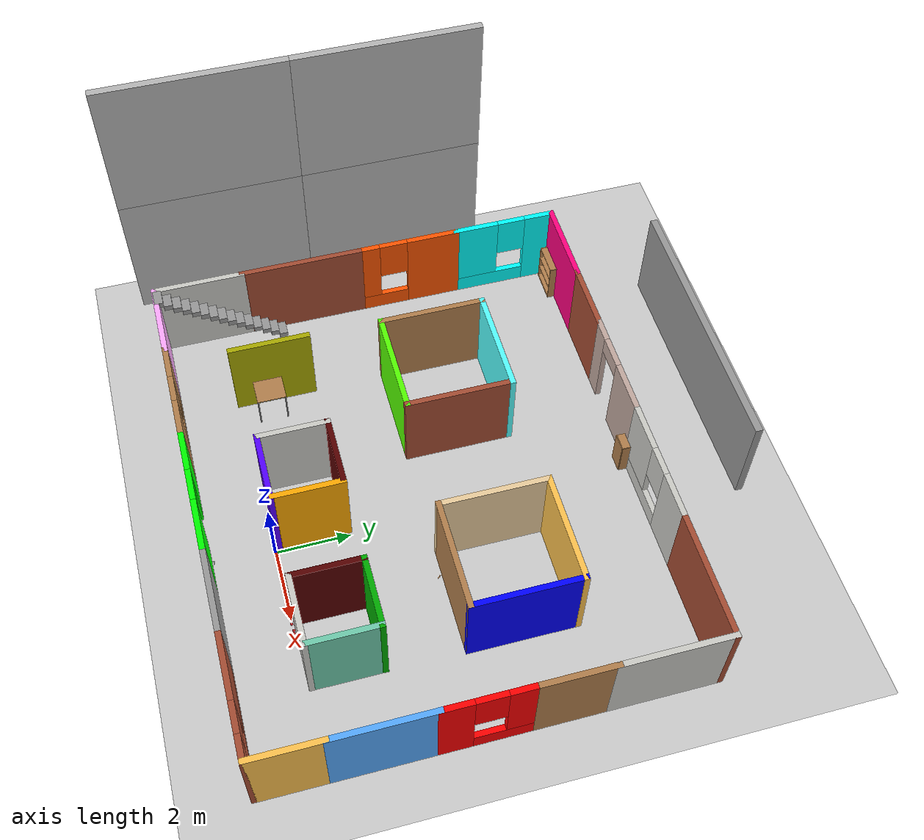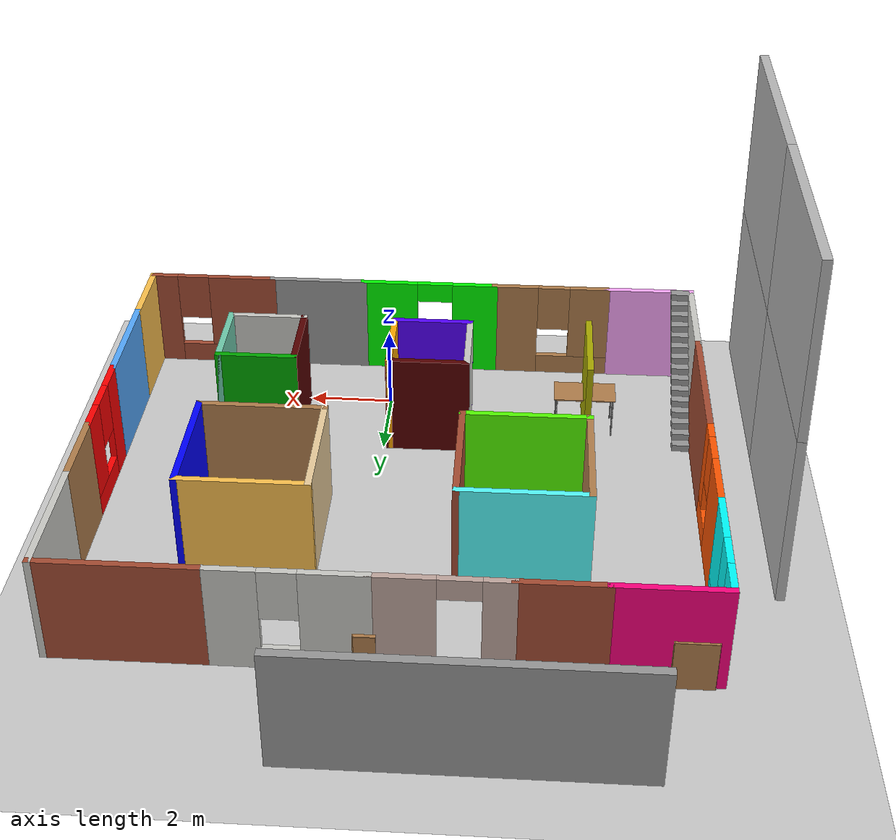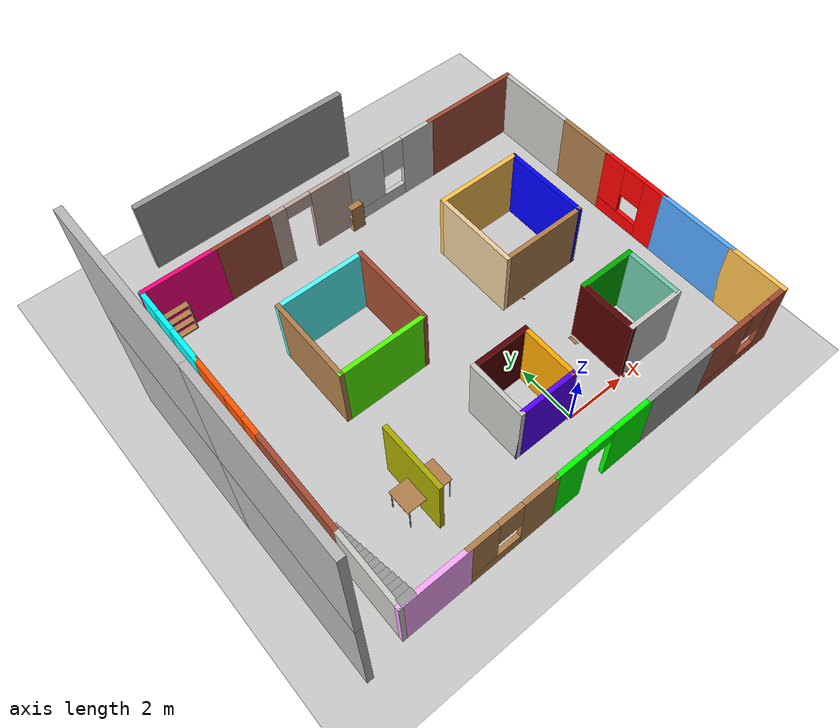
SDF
<sdf version="1.7">
 <world name="default">
  <light name="sun" type="directional">
   <pose>0 0 10 0 -0 0</pose>
   <diffuse>0.8 0.8 0.8 1</diffuse>
   <specular>0.2 0.2 0.2 1</specular>
   <attenuation>
    <range>1000</range>
    <constant>0.9</constant>
    <linear>0.01</linear>
    <quadratic>0.001</quadratic>
   </attenuation>
   <direction>-0.5 0.1 -0.9</direction>
   <spot><inner_angle>0</inner_angle><outer_angle>0</outer_angle><falloff>0</falloff></spot>
  </light>
  <physics type="ode">
   <real_time_update_rate>1000.0</real_time_update_rate>
   <max_step_size>0.001</max_step_size>
   <real_time_factor>1</real_time_factor>
   <ode>
    <solver>
     <type>quick</type>
     <iters>150</iters>
     <precon_iters>0</precon_iters>
     <sor>1.400000</sor>
     <use_dynamic_moi_rescaling>1</use_dynamic_moi_rescaling>
    </solver>
    <constraints>
     <cfm>0.00001</cfm>
     <erp>0.2</erp>
     <contact_max_correcting_vel>2000.000000</contact_max_correcting_vel>
     <contact_surface_layer>0.01000</contact_surface_layer>
    </constraints>
   </ode>
  </physics>
  <model name="ground_plane">
   <static>1</static>
   <link name="link">
    <collision name="collision">
     <geometry><plane><normal>0 0 1</normal><size>100 100</size></plane></geometry>
     <surface><friction><ode><mu>100</mu><mu2>50</mu2></ode></friction></surface>
    </collision>
    <visual name="visual">
     <cast_shadows>0</cast_shadows>
     <geometry><plane><normal>0 0 1</normal><size>100 100</size></plane></geometry>
     <material>
      <script><uri>file://media/materials/scripts/gazebo.material</uri><name>Gazebo/Grey</name></script>
     </material>
    </visual>
   </link>
  </model>
  <gravity>0 0 -9.8</gravity>
  <magnetic_field>6e-06 2.3e-05 -4.2e-05</magnetic_field>
  <atmosphere type="adiabatic"/>
  <physics type="ode">
   <max_step_size>0.001</max_step_size>
   <real_time_factor>1</real_time_factor>
   <real_time_update_rate>1000</real_time_update_rate>
  </physics>
  <scene><ambient>0.4 0.4 0.4 1</ambient><background>0.7 0.7 0.7 1</background><shadows>1</shadows></scene>
  <spherical_coordinates>
   <surface_model>EARTH_WGS84</surface_model>
   <latitude_deg>0</latitude_deg>
   <longitude_deg>0</longitude_deg>
   <elevation>0</elevation>
   <heading_deg>0</heading_deg>
  </spherical_coordinates>
  <model name="rainbow_house">
   <pose>-0.62277 4.02769 0 0 -0 0</pose>
   <link name="Stairs_0">
    <visual name="Stairs_0_Visual_0">
     <pose>-6.6068 -2.41526 0.083333 0 -0 0</pose>
     <geometry><box><size>0.454216 0.233333 0.166667</size></box></geometry>
     <material>
      <script><uri>file://media/materials/scripts/gazebo.material</uri><name>Gazebo/Grey</name></script>
      <ambient>1 1 1 1</ambient>
     </material>
     <meta><layer>0</layer></meta>
    </visual>
    <collision name="Stairs_0_Collision_0">
     <geometry><box><size>0.454216 0.233333 0.166667</size></box></geometry>
     <pose>-6.6068 -2.41526 0.083333 0 -0 0</pose>
    </collision>
    <visual name="Stairs_0_Visual_1">
     <pose>-6.6068 -2.64859 0.25 0 -0 0</pose>
     <geometry><box><size>0.454216 0.233333 0.166667</size></box></geometry>
     <material>
      <script><uri>file://media/materials/scripts/gazebo.material</uri><name>Gazebo/Grey</name></script>
      <ambient>1 1 1 1</ambient>
     </material>
     <meta><layer>0</layer></meta>
    </visual>
    <collision name="Stairs_0_Collision_1">
     <geometry><box><size>0.454216 0.233333 0.166667</size></box></geometry>
     <pose>-6.6068 -2.64859 0.25 0 -0 0</pose>
    </collision>
    <visual name="Stairs_0_Visual_2">
     <pose>-6.6068 -2.88193 0.416667 0 -0 0</pose>
     <geometry><box><size>0.454216 0.233333 0.166667</size></box></geometry>
     <material>
      <script><uri>file://media/materials/scripts/gazebo.material</uri><name>Gazebo/Grey</name></script>
      <ambient>1 1 1 1</ambient>
     </material>
     <meta><layer>0</layer></meta>
    </visual>
    <collision name="Stairs_0_Collision_2">
     <geometry><box><size>0.454216 0.233333 0.166667</size></box></geometry>
     <pose>-6.6068 -2.88193 0.416667 0 -0 0</pose>
    </collision>
    <visual name="Stairs_0_Visual_3">
     <pose>-6.6068 -3.11526 0.583333 0 -0 0</pose>
     <geometry><box><size>0.454216 0.233333 0.166667</size></box></geometry>
     <material>
      <script><uri>file://media/materials/scripts/gazebo.material</uri><name>Gazebo/Grey</name></script>
      <ambient>1 1 1 1</ambient>
     </material>
     <meta><layer>0</layer></meta>
    </visual>
    <collision name="Stairs_0_Collision_3">
     <geometry><box><size>0.454216 0.233333 0.166667</size></box></geometry>
     <pose>-6.6068 -3.11526 0.583333 0 -0 0</pose>
    </collision>
    <visual name="Stairs_0_Visual_4">
     <pose>-6.6068 -3.34859 0.75 0 -0 0</pose>
     <geometry><box><size>0.454216 0.233333 0.166667</size></box></geometry>
     <material>
      <script><uri>file://media/materials/scripts/gazebo.material</uri><name>Gazebo/Grey</name></script>
      <ambient>1 1 1 1</ambient>
     </material>
     <meta><layer>0</layer></meta>
    </visual>
    <collision name="Stairs_0_Collision_4">
     <geometry><box><size>0.454216 0.233333 0.166667</size></box></geometry>
     <pose>-6.6068 -3.34859 0.75 0 -0 0</pose>
    </collision>
    <visual name="Stairs_0_Visual_5">
     <pose>-6.6068 -3.58193 0.916667 0 -0 0</pose>
     <geometry><box><size>0.454216 0.233333 0.166667</size></box></geometry>
     <material>
      <script><uri>file://media/materials/scripts/gazebo.material</uri><name>Gazebo/Grey</name></script>
      <ambient>1 1 1 1</ambient>
     </material>
     <meta><layer>0</layer></meta>
    </visual>
    <collision name="Stairs_0_Collision_5">
     <geometry><box><size>0.454216 0.233333 0.166667</size></box></geometry>
     <pose>-6.6068 -3.58193 0.916667 0 -0 0</pose>
    </collision>
    <visual name="Stairs_0_Visual_6">
     <pose>-6.6068 -3.81526 1.08333 0 -0 0</pose>
     <geometry><box><size>0.454216 0.233333 0.166667</size></box></geometry>
     <material>
      <script><uri>file://media/materials/scripts/gazebo.material</uri><name>Gazebo/Grey</name></script>
      <ambient>1 1 1 1</ambient>
     </material>
     <meta><layer>0</layer></meta>
    </visual>
    <collision name="Stairs_0_Collision_6">
     <geometry><box><size>0.454216 0.233333 0.166667</size></box></geometry>
     <pose>-6.6068 -3.81526 1.08333 0 -0 0</pose>
    </collision>
    <visual name="Stairs_0_Visual_7">
     <pose>-6.6068 -4.04859 1.25 0 -0 0</pose>
     <geometry><box><size>0.454216 0.233333 0.166667</size></box></geometry>
     <material>
      <script><uri>file://media/materials/scripts/gazebo.material</uri><name>Gazebo/Grey</name></script>
      <ambient>1 1 1 1</ambient>
     </material>
     <meta><layer>0</layer></meta>
    </visual>
    <collision name="Stairs_0_Collision_7">
     <geometry><box><size>0.454216 0.233333 0.166667</size></box></geometry>
     <pose>-6.6068 -4.04859 1.25 0 -0 0</pose>
    </collision>
    <visual name="Stairs_0_Visual_8">
     <pose>-6.6068 -4.28193 1.41667 0 -0 0</pose>
     <geometry><box><size>0.454216 0.233333 0.166667</size></box></geometry>
     <material>
      <script><uri>file://media/materials/scripts/gazebo.material</uri><name>Gazebo/Grey</name></script>
      <ambient>1 1 1 1</ambient>
     </material>
     <meta><layer>0</layer></meta>
    </visual>
    <collision name="Stairs_0_Collision_8">
     <geometry><box><size>0.454216 0.233333 0.166667</size></box></geometry>
     <pose>-6.6068 -4.28193 1.41667 0 -0 0</pose>
    </collision>
    <visual name="Stairs_0_Visual_9">
     <pose>-6.6068 -4.51526 1.58333 0 -0 0</pose>
     <geometry><box><size>0.454216 0.233333 0.166667</size></box></geometry>
     <material>
      <script><uri>file://media/materials/scripts/gazebo.material</uri><name>Gazebo/Grey</name></script>
      <ambient>1 1 1 1</ambient>
     </material>
     <meta><layer>0</layer></meta>
    </visual>
    <collision name="Stairs_0_Collision_9">
     <geometry><box><size>0.454216 0.233333 0.166667</size></box></geometry>
     <pose>-6.6068 -4.51526 1.58333 0 -0 0</pose>
    </collision>
    <visual name="Stairs_0_Visual_10">
     <pose>-6.6068 -4.74859 1.75 0 -0 0</pose>
     <geometry><box><size>0.454216 0.233333 0.166667</size></box></geometry>
     <material>
      <script><uri>file://media/materials/scripts/gazebo.material</uri><name>Gazebo/Grey</name></script>
      <ambient>1 1 1 1</ambient>
     </material>
     <meta><layer>0</layer></meta>
    </visual>
    <collision name="Stairs_0_Collision_10">
     <geometry><box><size>0.454216 0.233333 0.166667</size></box></geometry>
     <pose>-6.6068 -4.74859 1.75 0 -0 0</pose>
    </collision>
    <visual name="Stairs_0_Visual_11">
     <pose>-6.6068 -4.98193 1.91667 0 -0 0</pose>
     <geometry><box><size>0.454216 0.233333 0.166667</size></box></geometry>
     <material>
      <script><uri>file://media/materials/scripts/gazebo.material</uri><name>Gazebo/Grey</name></script>
      <ambient>1 1 1 1</ambient>
     </material>
     <meta><layer>0</layer></meta>
    </visual>
    <collision name="Stairs_0_Collision_11">
     <geometry><box><size>0.454216 0.233333 0.166667</size></box></geometry>
     <pose>-6.6068 -4.98193 1.91667 0 -0 0</pose>
    </collision>
    <visual name="Stairs_0_Visual_12">
     <pose>-6.6068 -5.21526 2.08333 0 -0 0</pose>
     <geometry><box><size>0.454216 0.233333 0.166667</size></box></geometry>
     <material>
      <script><uri>file://media/materials/scripts/gazebo.material</uri><name>Gazebo/Grey</name></script>
      <ambient>1 1 1 1</ambient>
     </material>
     <meta><layer>0</layer></meta>
    </visual>
    <collision name="Stairs_0_Collision_12">
     <geometry><box><size>0.454216 0.233333 0.166667</size></box></geometry>
     <pose>-6.6068 -5.21526 2.08333 0 -0 0</pose>
    </collision>
    <visual name="Stairs_0_Visual_13">
     <pose>-6.6068 -5.44859 2.25 0 -0 0</pose>
     <geometry><box><size>0.454216 0.233333 0.166667</size></box></geometry>
     <material>
      <script><uri>file://media/materials/scripts/gazebo.material</uri><name>Gazebo/Grey</name></script>
      <ambient>1 1 1 1</ambient>
     </material>
     <meta><layer>0</layer></meta>
    </visual>
    <collision name="Stairs_0_Collision_13">
     <geometry><box><size>0.454216 0.233333 0.166667</size></box></geometry>
     <pose>-6.6068 -5.44859 2.25 0 -0 0</pose>
    </collision>
    <visual name="Stairs_0_Visual_14">
     <pose>-6.6068 -5.68193 2.41667 0 -0 0</pose>
     <geometry><box><size>0.454216 0.233333 0.166667</size></box></geometry>
     <material>
      <script><uri>file://media/materials/scripts/gazebo.material</uri><name>Gazebo/Grey</name></script>
      <ambient>1 1 1 1</ambient>
     </material>
     <meta><layer>0</layer></meta>
    </visual>
    <collision name="Stairs_0_Collision_14">
     <geometry><box><size>0.454216 0.233333 0.166667</size></box></geometry>
     <pose>-6.6068 -5.68193 2.41667 0 -0 0</pose>
    </collision>
   </link>
   <link name="Wall_10">
    <collision name="Wall_10_Collision">
     <geometry><box><size>2 0.15 2.5</size></box></geometry>
     <pose>0 0 1.25 0 -0 0</pose>
    </collision>
    <visual name="Wall_10_Visual">
     <pose>0 0 1.25 0 -0 0</pose>
     <geometry><box><size>2 0.15 2.5</size></box></geometry>
     <material>
      <script><uri>file://media/materials/scripts/gazebo.material</uri><name>Gazebo/Grey</name></script>
      <ambient>0.333333 0 0 1</ambient>
     </material>
     <meta><layer>0</layer></meta>
    </visual>
    <pose>2.71455 -2.97747 0 0 -0 1.5708</pose>
   </link>
   <link name="Wall_11">
    <collision name="Wall_11_Collision">
     <geometry><box><size>1.96045 0.15 2.5</size></box></geometry>
     <pose>0 0 1.25 0 -0 0</pose>
    </collision>
    <visual name="Wall_11_Visual">
     <pose>0 0 1.25 0 -0 0</pose>
     <geometry><box><size>1.96045 0.15 2.5</size></box></geometry>
     <material>
      <script><uri>file://media/materials/scripts/gazebo.material</uri><name>Gazebo/Grey</name></script>
      <ambient>0 0.666667 0 1</ambient>
     </material>
     <meta><layer>0</layer></meta>
    </visual>
    <pose>3.61978 -2.05 0 0 -0 0</pose>
   </link>
   <link name="Wall_12">
    <collision name="Wall_12_Collision">
     <geometry><box><size>2 0.15 2.5</size></box></geometry>
     <pose>0 0 1.25 0 -0 0</pose>
    </collision>
    <visual name="Wall_12_Visual">
     <pose>0 0 1.25 0 -0 0</pose>
     <geometry><box><size>2 0.15 2.5</size></box></geometry>
     <material>
      <script><uri>file://media/materials/scripts/gazebo.material</uri><name>Gazebo/Grey</name></script>
      <ambient>0.435294 0.796078 0.67451 1</ambient>
     </material>
     <meta><layer>0</layer></meta>
    </visual>
    <pose>4.52253 -2.975 0 0 -0 -1.5708</pose>
   </link>
   <link name="Wall_13">
    <collision name="Wall_13_Collision">
     <geometry><box><size>1.96045 0.15 2.5</size></box></geometry>
     <pose>0 0 1.25 0 -0 0</pose>
    </collision>
    <visual name="Wall_13_Visual">
     <pose>0 0 1.25 0 -0 0</pose>
     <geometry><box><size>1.96045 0.15 2.5</size></box></geometry>
     <material>
      <script><uri>file://media/materials/scripts/gazebo.material</uri><name>Gazebo/CeilingTiled</name></script>
      <ambient>1 1 1 1</ambient>
     </material>
     <meta><layer>0</layer></meta>
    </visual>
    <pose>3.61978 -3.9 0 0 -0 3.14159</pose>
   </link>
   <link name="Wall_2">
    <collision name="Wall_2_Collision">
     <geometry><box><size>2 0.15 2.5</size></box></geometry>
     <pose>0 0 1.25 0 -0 0</pose>
    </collision>
    <visual name="Wall_2_Visual">
     <pose>0 0 1.25 0 -0 0</pose>
     <geometry><box><size>2 0.15 2.5</size></box></geometry>
     <material>
      <script><uri>file://media/materials/scripts/gazebo.material</uri><name>Gazebo/CeilingTiled</name></script>
      <ambient>0.435294 0.796078 0.67451 1</ambient>
     </material>
     <meta><layer>0</layer></meta>
    </visual>
    <pose>-1.38095 -2.975 0 0 -0 1.5708</pose>
   </link>
   <link name="Wall_22">
    <collision name="Wall_22_Collision">
     <geometry><box><size>3 0.15 2.5</size></box></geometry>
     <pose>0 0 1.25 0 -0 0</pose>
    </collision>
    <visual name="Wall_22_Visual">
     <pose>0 0 1.25 0 -0 0</pose>
     <geometry><box><size>3 0.15 2.5</size></box></geometry>
     <material>
      <script><uri>file://media/materials/scripts/gazebo.material</uri><name>Gazebo/Wood</name></script>
      <ambient>1 1 1 1</ambient>
     </material>
     <meta><layer>0</layer></meta>
    </visual>
    <pose>3.14584 0.047664 0 0 -0 3.14159</pose>
   </link>
   <link name="Wall_25">
    <collision name="Wall_25_Collision">
     <geometry><box><size>3 0.15 2.5</size></box></geometry>
     <pose>0 0 1.25 0 -0 0</pose>
    </collision>
    <visual name="Wall_25_Visual">
     <pose>0 0 1.25 0 -0 0</pose>
     <geometry><box><size>3 0.15 2.5</size></box></geometry>
     <material>
      <script><uri>file://media/materials/scripts/gazebo.material</uri><name>Gazebo/Grey</name></script>
      <ambient>0 0 1 1</ambient>
     </material>
     <meta><layer>0</layer></meta>
    </visual>
    <pose>4.57084 1.47266 0 0 -0 1.5708</pose>
   </link>
   <link name="Wall_26">
    <collision name="Wall_26_Collision">
     <geometry><box><size>3 0.15 2.5</size></box></geometry>
     <pose>0 0 1.25 0 -0 0</pose>
    </collision>
    <visual name="Wall_26_Visual">
     <pose>0 0 1.25 0 -0 0</pose>
     <geometry><box><size>3 0.15 2.5</size></box></geometry>
     <material>
      <script><uri>file://media/materials/scripts/gazebo.material</uri><name>Gazebo/Grey</name></script>
      <ambient>1 0.764706 0.305882 1</ambient>
     </material>
     <meta><layer>0</layer></meta>
    </visual>
    <pose>3.14584 2.89766 0 0 -0 3.14159</pose>
   </link>
   <link name="Wall_27">
    <collision name="Wall_27_Collision">
     <geometry><box><size>3 0.15 2.5</size></box></geometry>
     <pose>0 0 1.25 0 -0 0</pose>
    </collision>
    <visual name="Wall_27_Visual">
     <pose>0 0 1.25 0 -0 0</pose>
     <geometry><box><size>3 0.15 2.5</size></box></geometry>
     <material>
      <script><uri>file://media/materials/scripts/gazebo.material</uri><name>Gazebo/Grey</name></script>
      <ambient>0.921569 0.807843 0.615686 1</ambient>
     </material>
     <meta><layer>0</layer></meta>
    </visual>
    <pose>1.72084 1.47266 0 0 -0 -1.5708</pose>
   </link>
   <link name="Wall_33">
    <collision name="Wall_33_Collision">
     <geometry><box><size>3 0.15 2.5</size></box></geometry>
     <pose>0 0 1.25 0 -0 0</pose>
    </collision>
    <visual name="Wall_33_Visual">
     <pose>0 0 1.25 0 -0 0</pose>
     <geometry><box><size>3 0.15 2.5</size></box></geometry>
     <material>
      <script><uri>file://media/materials/scripts/gazebo.material</uri><name>Gazebo/Bricks</name></script>
      <ambient>1 1 1 1</ambient>
     </material>
     <meta><layer>0</layer></meta>
    </visual>
    <pose>-1.37916 1.47266 0 0 -0 1.5708</pose>
   </link>
   <link name="Wall_34">
    <collision name="Wall_34_Collision">
     <geometry><box><size>3 0.15 2.5</size></box></geometry>
     <pose>0 0 1.25 0 -0 0</pose>
    </collision>
    <visual name="Wall_34_Visual">
     <pose>0 0 1.25 0 -0 0</pose>
     <geometry><box><size>3 0.15 2.5</size></box></geometry>
     <material>
      <script><uri>file://media/materials/scripts/gazebo.material</uri><name>Gazebo/Grey</name></script>
      <ambient>0.333333 1 1 1</ambient>
     </material>
     <meta><layer>0</layer></meta>
    </visual>
    <pose>-2.80416 2.89766 0 0 -0 3.14159</pose>
   </link>
   <link name="Wall_35">
    <collision name="Wall_35_Collision">
     <geometry><box><size>3 0.15 2.5</size></box></geometry>
     <pose>0 0 1.25 0 -0 0</pose>
    </collision>
    <visual name="Wall_35_Visual">
     <pose>0 0 1.25 0 -0 0</pose>
     <geometry><box><size>3 0.15 2.5</size></box></geometry>
     <material>
      <script><uri>file://media/materials/scripts/gazebo.material</uri><name>Gazebo/Wood</name></script>
      <ambient>1 1 1 1</ambient>
     </material>
     <meta><layer>0</layer></meta>
    </visual>
    <pose>-4.22916 1.47266 0 0 -0 -1.5708</pose>
   </link>
   <link name="Wall_36">
    <collision name="Wall_36_Collision">
     <geometry><box><size>3 0.15 2.5</size></box></geometry>
     <pose>0 0 1.25 0 -0 0</pose>
    </collision>
    <visual name="Wall_36_Visual">
     <pose>0 0 1.25 0 -0 0</pose>
     <geometry><box><size>3 0.15 2.5</size></box></geometry>
     <material>
      <script><uri>file://media/materials/scripts/gazebo.material</uri><name>Gazebo/Grey</name></script>
      <ambient>0.333333 1 0 1</ambient>
     </material>
     <meta><layer>0</layer></meta>
    </visual>
    <pose>-2.80416 0.047664 0 0 -0 0</pose>
   </link>
   <link name="Wall_4">
    <collision name="Wall_4_Collision">
     <geometry><box><size>2 0.15 2.5</size></box></geometry>
     <pose>0 0 1.25 0 -0 0</pose>
    </collision>
    <visual name="Wall_4_Visual">
     <pose>0 0 1.25 0 -0 0</pose>
     <geometry><box><size>2 0.15 2.5</size></box></geometry>
     <material>
      <script><uri>file://media/materials/scripts/gazebo.material</uri><name>Gazebo/Grey</name></script>
      <ambient>0.333333 0 0 1</ambient>
     </material>
     <meta><layer>0</layer></meta>
    </visual>
    <pose>-0.455946 -2.05 0 0 -0 0</pose>
   </link>
   <link name="Wall_42">
    <collision name="Wall_42_Collision">
     <geometry><box><size>2 0.15 2.5</size></box></geometry>
     <pose>0 0 1.25 0 -0 0</pose>
    </collision>
    <visual name="Wall_42_Visual">
     <pose>0 0 1.25 0 -0 0</pose>
     <geometry><box><size>2 0.15 2.5</size></box></geometry>
     <material>
      <script><uri>file://media/materials/scripts/gazebo.material</uri><name>Gazebo/Grey</name></script>
      <ambient>1 0.764706 0.305882 1</ambient>
     </material>
     <meta><layer>0</layer></meta>
    </visual>
    <pose>6.875 -4.825 0 0 -0 -1.5708</pose>
   </link>
   <link name="Wall_44">
    <collision name="Wall_44_Collision">
     <geometry><box><size>2.75 0.15 2.5</size></box></geometry>
     <pose>0 0 1.25 0 -0 0</pose>
    </collision>
    <visual name="Wall_44_Visual">
     <pose>0 0 1.25 0 -0 0</pose>
     <geometry><box><size>2.75 0.15 2.5</size></box></geometry>
     <material>
      <script><uri>file://media/materials/scripts/gazebo.material</uri><name>Gazebo/Grey</name></script>
      <ambient>0.333333 0.666667 1 1</ambient>
     </material>
     <meta><layer>0</layer></meta>
    </visual>
    <pose>6.875 -2.6 0 0 -0 1.5708</pose>
   </link>
   <link name="Wall_45">
    <pose>6.875 -0.125 0 0 -0 1.5708</pose>
    <visual name="Wall_45_Visual_0">
     <pose>-0.81636 0 1.25 0 -0 0</pose>
     <geometry><box><size>0.86728 0.15 2.5</size></box></geometry>
     <material>
      <script><uri>file://media/materials/scripts/gazebo.material</uri><name>Gazebo/Grey</name></script>
      <ambient>1 0 0 1</ambient>
     </material>
     <meta><layer>0</layer></meta>
    </visual>
    <collision name="Wall_45_Collision_0">
     <geometry><box><size>0.86728 0.15 2.5</size></box></geometry>
     <pose>-0.81636 0 1.25 0 -0 0</pose>
    </collision>
    <visual name="Wall_45_Visual_1">
     <pose>0.43364 0 0.25 0 -0 0</pose>
     <geometry><box><size>1.63272 0.15 0.5</size></box></geometry>
     <material>
      <script><uri>file://media/materials/scripts/gazebo.material</uri><name>Gazebo/Grey</name></script>
      <ambient>1 0 0 1</ambient>
     </material>
     <meta><layer>0</layer></meta>
    </visual>
    <collision name="Wall_45_Collision_1">
     <geometry><box><size>1.63272 0.15 0.5</size></box></geometry>
     <pose>0.43364 0 0.25 0 -0 0</pose>
    </collision>
    <visual name="Wall_45_Visual_2">
     <pose>0.83364 0 1.5 0 -0 0</pose>
     <geometry><box><size>0.83272 0.15 2</size></box></geometry>
     <material>
      <script><uri>file://media/materials/scripts/gazebo.material</uri><name>Gazebo/Grey</name></script>
      <ambient>1 0 0 1</ambient>
     </material>
     <meta><layer>0</layer></meta>
    </visual>
    <collision name="Wall_45_Collision_2">
     <geometry><box><size>0.83272 0.15 2</size></box></geometry>
     <pose>0.83364 0 1.5 0 -0 0</pose>
    </collision>
    <visual name="Wall_45_Visual_3">
     <pose>0.01728 0 1.9 0 -0 0</pose>
     <geometry><box><size>0.8 0.15 1.2</size></box></geometry>
     <material>
      <script><uri>file://media/materials/scripts/gazebo.material</uri><name>Gazebo/Grey</name></script>
      <ambient>1 0 0 1</ambient>
     </material>
     <meta><layer>0</layer></meta>
    </visual>
    <collision name="Wall_45_Collision_3">
     <geometry><box><size>0.8 0.15 1.2</size></box></geometry>
     <pose>0.01728 0 1.9 0 -0 0</pose>
    </collision>
   </link>
   <link name="Wall_46">
    <collision name="Wall_46_Collision">
     <geometry><box><size>2 0.15 2.5</size></box></geometry>
     <pose>0 0 1.25 0 -0 0</pose>
    </collision>
    <visual name="Wall_46_Visual">
     <pose>0 0 1.25 0 -0 0</pose>
     <geometry><box><size>2 0.15 2.5</size></box></geometry>
     <material>
      <script><uri>file://media/materials/scripts/gazebo.material</uri><name>Gazebo/Wood</name></script>
      <ambient>1 1 1 1</ambient>
     </material>
     <meta><layer>0</layer></meta>
    </visual>
    <pose>6.875 1.975 0 0 -0 1.5708</pose>
   </link>
   <link name="Wall_48">
    <collision name="Wall_48_Collision">
     <geometry><box><size>3 0.15 2.5</size></box></geometry>
     <pose>0 0 1.25 0 -0 0</pose>
    </collision>
    <visual name="Wall_48_Visual">
     <pose>0 0 1.25 0 -0 0</pose>
     <geometry><box><size>3 0.15 2.5</size></box></geometry>
     <material>
      <script><uri>file://media/materials/scripts/gazebo.material</uri><name>Gazebo/CeilingTiled</name></script>
      <ambient>1 1 1 1</ambient>
     </material>
     <meta><layer>0</layer></meta>
    </visual>
    <pose>6.875 4.325 0 0 -0 1.5708</pose>
   </link>
   <link name="Wall_49">
    <collision name="Wall_49_Collision">
     <geometry><box><size>3.5 0.15 2.5</size></box></geometry>
     <pose>0 0 1.25 0 -0 0</pose>
    </collision>
    <visual name="Wall_49_Visual">
     <pose>0 0 1.25 0 -0 0</pose>
     <geometry><box><size>3.5 0.15 2.5</size></box></geometry>
     <material>
      <script><uri>file://media/materials/scripts/gazebo.material</uri><name>Gazebo/Bricks</name></script>
      <ambient>1 1 1 1</ambient>
     </material>
     <meta><layer>0</layer></meta>
    </visual>
    <pose>5.2 5.75 0 0 -0 3.14159</pose>
   </link>
   <link name="Wall_5">
    <collision name="Wall_5_Collision">
     <geometry><box><size>2 0.15 2.5</size></box></geometry>
     <pose>0 0 1.25 0 -0 0</pose>
    </collision>
    <visual name="Wall_5_Visual">
     <pose>0 0 1.25 0 -0 0</pose>
     <geometry><box><size>2 0.15 2.5</size></box></geometry>
     <material>
      <script><uri>file://media/materials/scripts/gazebo.material</uri><name>Gazebo/Grey</name></script>
      <ambient>1 0.666667 0 1</ambient>
     </material>
     <meta><layer>0</layer></meta>
    </visual>
    <pose>0.469054 -2.975 0 0 -0 -1.5708</pose>
   </link>
   <link name="Wall_50">
    <pose>1.85 5.75 0 0 -0 3.14159</pose>
    <visual name="Wall_50_Visual_0">
     <pose>-1.13041 0 1.25 0 -0 0</pose>
     <geometry><box><size>1.23918 0.15 2.5</size></box></geometry>
     <material>
      <script><uri>file://media/materials/scripts/gazebo.material</uri><name>Gazebo/CeilingTiled</name></script>
      <ambient>1 1 1 1</ambient>
     </material>
     <meta><layer>0</layer></meta>
    </visual>
    <collision name="Wall_50_Collision_0">
     <geometry><box><size>1.23918 0.15 2.5</size></box></geometry>
     <pose>-1.13041 0 1.25 0 -0 0</pose>
    </collision>
    <visual name="Wall_50_Visual_1">
     <pose>0.619589 0 0.25 0 -0 0</pose>
     <geometry><box><size>2.26082 0.15 0.5</size></box></geometry>
     <material>
      <script><uri>file://media/materials/scripts/gazebo.material</uri><name>Gazebo/CeilingTiled</name></script>
      <ambient>1 1 1 1</ambient>
     </material>
     <meta><layer>0</layer></meta>
    </visual>
    <collision name="Wall_50_Collision_1">
     <geometry><box><size>2.26082 0.15 0.5</size></box></geometry>
     <pose>0.619589 0 0.25 0 -0 0</pose>
    </collision>
    <visual name="Wall_50_Visual_2">
     <pose>1.01959 0 1.5 0 -0 0</pose>
     <geometry><box><size>1.46082 0.15 2</size></box></geometry>
     <material>
      <script><uri>file://media/materials/scripts/gazebo.material</uri><name>Gazebo/CeilingTiled</name></script>
      <ambient>1 1 1 1</ambient>
     </material>
     <meta><layer>0</layer></meta>
    </visual>
    <collision name="Wall_50_Collision_2">
     <geometry><box><size>1.46082 0.15 2</size></box></geometry>
     <pose>1.01959 0 1.5 0 -0 0</pose>
    </collision>
    <visual name="Wall_50_Visual_3">
     <pose>-0.110823 0 1.9 0 -0 0</pose>
     <geometry><box><size>0.8 0.15 1.2</size></box></geometry>
     <material>
      <script><uri>file://media/materials/scripts/gazebo.material</uri><name>Gazebo/CeilingTiled</name></script>
      <ambient>1 1 1 1</ambient>
     </material>
     <meta><layer>0</layer></meta>
    </visual>
    <collision name="Wall_50_Collision_3">
     <geometry><box><size>0.8 0.15 1.2</size></box></geometry>
     <pose>-0.110823 0 1.9 0 -0 0</pose>
    </collision>
   </link>
   <link name="Wall_52">
    <pose>-1.25 5.75 0 0 -0 3.14159</pose>
    <visual name="Wall_52_Visual_0">
     <pose>-0.796809 0 1.25 0 -0 0</pose>
     <geometry><box><size>1.40638 0.15 2.5</size></box></geometry>
     <material>
      <script><uri>file://media/materials/scripts/gazebo.material</uri><name>Gazebo/Grey</name></script>
      <ambient>0.760784 0.662745 0.627451 1</ambient>
     </material>
     <meta><layer>0</layer></meta>
    </visual>
    <collision name="Wall_52_Collision_0">
     <geometry><box><size>1.40638 0.15 2.5</size></box></geometry>
     <pose>-0.796809 0 1.25 0 -0 0</pose>
    </collision>
    <visual name="Wall_52_Visual_1">
     <pose>1.15319 0 1.25 0 -0 0</pose>
     <geometry><box><size>0.693617 0.15 2.5</size></box></geometry>
     <material>
      <script><uri>file://media/materials/scripts/gazebo.material</uri><name>Gazebo/Grey</name></script>
      <ambient>0.760784 0.662745 0.627451 1</ambient>
     </material>
     <meta><layer>0</layer></meta>
    </visual>
    <collision name="Wall_52_Collision_1">
     <geometry><box><size>0.693617 0.15 2.5</size></box></geometry>
     <pose>1.15319 0 1.25 0 -0 0</pose>
    </collision>
    <visual name="Wall_52_Visual_2">
     <pose>0.356383 0 2.25 0 -0 0</pose>
     <geometry><box><size>0.9 0.15 0.5</size></box></geometry>
     <material>
      <script><uri>file://media/materials/scripts/gazebo.material</uri><name>Gazebo/Grey</name></script>
      <ambient>0.760784 0.662745 0.627451 1</ambient>
     </material>
     <meta><layer>0</layer></meta>
    </visual>
    <collision name="Wall_52_Collision_2">
     <geometry><box><size>0.9 0.15 0.5</size></box></geometry>
     <pose>0.356383 0 2.25 0 -0 0</pose>
    </collision>
   </link>
   <link name="Wall_53">
    <collision name="Wall_53_Collision">
     <geometry><box><size>2 0.15 2.5</size></box></geometry>
     <pose>0 0 1.25 0 -0 0</pose>
    </collision>
    <visual name="Wall_53_Visual">
     <pose>0 0 1.25 0 -0 0</pose>
     <geometry><box><size>2 0.15 2.5</size></box></geometry>
     <material>
      <script><uri>file://media/materials/scripts/gazebo.material</uri><name>Gazebo/Bricks</name></script>
      <ambient>1 1 1 1</ambient>
     </material>
     <meta><layer>0</layer></meta>
    </visual>
    <pose>-3.6 5.75 0 0 -0 3.14159</pose>
   </link>
   <link name="Wall_56">
    <collision name="Wall_56_Collision">
     <geometry><box><size>2.5 0.15 2.5</size></box></geometry>
     <pose>0 0 1.25 0 -0 0</pose>
    </collision>
    <visual name="Wall_56_Visual">
     <pose>0 0 1.25 0 -0 0</pose>
     <geometry><box><size>2.5 0.15 2.5</size></box></geometry>
     <material>
      <script><uri>file://media/materials/scripts/gazebo.material</uri><name>Gazebo/Grey</name></script>
      <ambient>1 0 0.498039 1</ambient>
     </material>
     <meta><layer>0</layer></meta>
    </visual>
    <pose>-5.7 5.75 0 0 -0 3.14159</pose>
   </link>
   <link name="Wall_57">
    <pose>-6.875 4.325 0 0 -0 -1.5708</pose>
    <visual name="Wall_57_Visual_0">
     <pose>-1.05348 0 1.25 0 -0 0</pose>
     <geometry><box><size>0.893041 0.15 2.5</size></box></geometry>
     <material>
      <script><uri>file://media/materials/scripts/gazebo.material</uri><name>Gazebo/Grey</name></script>
      <ambient>0 1 1 1</ambient>
     </material>
     <meta><layer>0</layer></meta>
    </visual>
    <collision name="Wall_57_Collision_0">
     <geometry><box><size>0.893041 0.15 2.5</size></box></geometry>
     <pose>-1.05348 0 1.25 0 -0 0</pose>
    </collision>
    <visual name="Wall_57_Visual_1">
     <pose>0.446521 0 0.25 0 -0 0</pose>
     <geometry><box><size>2.10696 0.15 0.5</size></box></geometry>
     <material>
      <script><uri>file://media/materials/scripts/gazebo.material</uri><name>Gazebo/Grey</name></script>
      <ambient>0 1 1 1</ambient>
     </material>
     <meta><layer>0</layer></meta>
    </visual>
    <collision name="Wall_57_Collision_1">
     <geometry><box><size>2.10696 0.15 0.5</size></box></geometry>
     <pose>0.446521 0 0.25 0 -0 0</pose>
    </collision>
    <visual name="Wall_57_Visual_2">
     <pose>0.846521 0 1.5 0 -0 0</pose>
     <geometry><box><size>1.30696 0.15 2</size></box></geometry>
     <material>
      <script><uri>file://media/materials/scripts/gazebo.material</uri><name>Gazebo/Grey</name></script>
      <ambient>0 1 1 1</ambient>
     </material>
     <meta><layer>0</layer></meta>
    </visual>
    <collision name="Wall_57_Collision_2">
     <geometry><box><size>1.30696 0.15 2</size></box></geometry>
     <pose>0.846521 0 1.5 0 -0 0</pose>
    </collision>
    <visual name="Wall_57_Visual_3">
     <pose>-0.206959 0 1.9 0 -0 0</pose>
     <geometry><box><size>0.8 0.15 1.2</size></box></geometry>
     <material>
      <script><uri>file://media/materials/scripts/gazebo.material</uri><name>Gazebo/Grey</name></script>
      <ambient>0 1 1 1</ambient>
     </material>
     <meta><layer>0</layer></meta>
    </visual>
    <collision name="Wall_57_Collision_3">
     <geometry><box><size>0.8 0.15 1.2</size></box></geometry>
     <pose>-0.206959 0 1.9 0 -0 0</pose>
    </collision>
   </link>
   <link name="Wall_58">
    <pose>-6.875 1.475 0 0 -0 -1.5708</pose>
    <visual name="Wall_58_Visual_0">
     <pose>-0.732658 0 1.25 0 -0 0</pose>
     <geometry><box><size>1.53468 0.15 2.5</size></box></geometry>
     <material>
      <script><uri>file://media/materials/scripts/gazebo.material</uri><name>Gazebo/Grey</name></script>
      <ambient>1 0.333333 0 1</ambient>
     </material>
     <meta><layer>0</layer></meta>
    </visual>
    <collision name="Wall_58_Collision_0">
     <geometry><box><size>1.53468 0.15 2.5</size></box></geometry>
     <pose>-0.732658 0 1.25 0 -0 0</pose>
    </collision>
    <visual name="Wall_58_Visual_1">
     <pose>0.767342 0 0.25 0 -0 0</pose>
     <geometry><box><size>1.46532 0.15 0.5</size></box></geometry>
     <material>
      <script><uri>file://media/materials/scripts/gazebo.material</uri><name>Gazebo/Grey</name></script>
      <ambient>1 0.333333 0 1</ambient>
     </material>
     <meta><layer>0</layer></meta>
    </visual>
    <collision name="Wall_58_Collision_1">
     <geometry><box><size>1.46532 0.15 0.5</size></box></geometry>
     <pose>0.767342 0 0.25 0 -0 0</pose>
    </collision>
    <visual name="Wall_58_Visual_2">
     <pose>1.16734 0 1.5 0 -0 0</pose>
     <geometry><box><size>0.665316 0.15 2</size></box></geometry>
     <material>
      <script><uri>file://media/materials/scripts/gazebo.material</uri><name>Gazebo/Grey</name></script>
      <ambient>1 0.333333 0 1</ambient>
     </material>
     <meta><layer>0</layer></meta>
    </visual>
    <collision name="Wall_58_Collision_2">
     <geometry><box><size>0.665316 0.15 2</size></box></geometry>
     <pose>1.16734 0 1.5 0 -0 0</pose>
    </collision>
    <visual name="Wall_58_Visual_3">
     <pose>0.434684 0 1.9 0 -0 0</pose>
     <geometry><box><size>0.8 0.15 1.2</size></box></geometry>
     <material>
      <script><uri>file://media/materials/scripts/gazebo.material</uri><name>Gazebo/Grey</name></script>
      <ambient>1 0.333333 0 1</ambient>
     </material>
     <meta><layer>0</layer></meta>
    </visual>
    <collision name="Wall_58_Collision_3">
     <geometry><box><size>0.8 0.15 1.2</size></box></geometry>
     <pose>0.434684 0 1.9 0 -0 0</pose>
    </collision>
   </link>
   <link name="Wall_6">
    <collision name="Wall_6_Collision">
     <geometry><box><size>2 0.15 2.5</size></box></geometry>
     <pose>0 0 1.25 0 -0 0</pose>
    </collision>
    <visual name="Wall_6_Visual">
     <pose>0 0 1.25 0 -0 0</pose>
     <geometry><box><size>2 0.15 2.5</size></box></geometry>
     <material>
      <script><uri>file://media/materials/scripts/gazebo.material</uri><name>Gazebo/Grey</name></script>
      <ambient>0.333333 0 1 1</ambient>
     </material>
     <meta><layer>0</layer></meta>
    </visual>
    <pose>-0.455946 -3.9 0 0 -0 3.14159</pose>
   </link>
   <link name="Wall_60">
    <collision name="Wall_60_Collision">
     <geometry><box><size>3.5 0.15 2.5</size></box></geometry>
     <pose>0 0 1.25 0 -0 0</pose>
    </collision>
    <visual name="Wall_60_Visual">
     <pose>0 0 1.25 0 -0 0</pose>
     <geometry><box><size>3.5 0.15 2.5</size></box></geometry>
     <material>
      <script><uri>file://media/materials/scripts/gazebo.material</uri><name>Gazebo/Bricks</name></script>
      <ambient>1 1 1 1</ambient>
     </material>
     <meta><layer>0</layer></meta>
    </visual>
    <pose>-6.875 -1.625 0 0 -0 -1.5708</pose>
   </link>
   <link name="Wall_63">
    <pose>5.325 -5.75 0 0 -0 3.14159</pose>
    <visual name="Wall_63_Visual_0">
     <pose>-1.26951 0 1.25 0 -0 0</pose>
     <geometry><box><size>0.710971 0.15 2.5</size></box></geometry>
     <material>
      <script><uri>file://media/materials/scripts/gazebo.material</uri><name>Gazebo/Bricks</name></script>
      <ambient>1 1 1 1</ambient>
     </material>
     <meta><layer>0</layer></meta>
    </visual>
    <collision name="Wall_63_Collision_0">
     <geometry><box><size>0.710971 0.15 2.5</size></box></geometry>
     <pose>-1.26951 0 1.25 0 -0 0</pose>
    </collision>
    <visual name="Wall_63_Visual_1">
     <pose>0.355486 0 0.25 0 -0 0</pose>
     <geometry><box><size>2.53903 0.15 0.5</size></box></geometry>
     <material>
      <script><uri>file://media/materials/scripts/gazebo.material</uri><name>Gazebo/Bricks</name></script>
      <ambient>1 1 1 1</ambient>
     </material>
     <meta><layer>0</layer></meta>
    </visual>
    <collision name="Wall_63_Collision_1">
     <geometry><box><size>2.53903 0.15 0.5</size></box></geometry>
     <pose>0.355486 0 0.25 0 -0 0</pose>
    </collision>
    <visual name="Wall_63_Visual_2">
     <pose>0.755486 0 1.5 0 -0 0</pose>
     <geometry><box><size>1.73903 0.15 2</size></box></geometry>
     <material>
      <script><uri>file://media/materials/scripts/gazebo.material</uri><name>Gazebo/Bricks</name></script>
      <ambient>1 1 1 1</ambient>
     </material>
     <meta><layer>0</layer></meta>
    </visual>
    <collision name="Wall_63_Collision_2">
     <geometry><box><size>1.73903 0.15 2</size></box></geometry>
     <pose>0.755486 0 1.5 0 -0 0</pose>
    </collision>
    <visual name="Wall_63_Visual_3">
     <pose>-0.514029 0 1.9 0 -0 0</pose>
     <geometry><box><size>0.8 0.15 1.2</size></box></geometry>
     <material>
      <script><uri>file://media/materials/scripts/gazebo.material</uri><name>Gazebo/Bricks</name></script>
      <ambient>1 1 1 1</ambient>
     </material>
     <meta><layer>0</layer></meta>
    </visual>
    <collision name="Wall_63_Collision_3">
     <geometry><box><size>0.8 0.15 1.2</size></box></geometry>
     <pose>-0.514029 0 1.9 0 -0 0</pose>
    </collision>
   </link>
   <link name="Wall_64">
    <collision name="Wall_64_Collision">
     <geometry><box><size>2.5 0.15 2.5</size></box></geometry>
     <pose>0 0 1.25 0 -0 0</pose>
    </collision>
    <visual name="Wall_64_Visual">
     <pose>0 0 1.25 0 -0 0</pose>
     <geometry><box><size>2.5 0.15 2.5</size></box></geometry>
     <material>
      <script><uri>file://media/materials/scripts/gazebo.material</uri><name>Gazebo/Grey</name></script>
      <ambient>0 0 0 1</ambient>
     </material>
     <meta><layer>0</layer></meta>
    </visual>
    <pose>2.6 -5.75 0 0 -0 3.14159</pose>
   </link>
   <link name="Wall_65">
    <pose>-0.25 -5.75 0 0 -0 3.14159</pose>
    <visual name="Wall_65_Visual_0">
     <pose>-1.02575 0 1.25 0 -0 0</pose>
     <geometry><box><size>1.44851 0.15 2.5</size></box></geometry>
     <material>
      <script><uri>file://media/materials/scripts/gazebo.material</uri><name>Gazebo/Grey</name></script>
      <ambient>0 1 0 1</ambient>
     </material>
     <meta><layer>0</layer></meta>
    </visual>
    <collision name="Wall_65_Collision_0">
     <geometry><box><size>1.44851 0.15 2.5</size></box></geometry>
     <pose>-1.02575 0 1.25 0 -0 0</pose>
    </collision>
    <visual name="Wall_65_Visual_1">
     <pose>1.17425 0 1.25 0 -0 0</pose>
     <geometry><box><size>1.15149 0.15 2.5</size></box></geometry>
     <material>
      <script><uri>file://media/materials/scripts/gazebo.material</uri><name>Gazebo/Grey</name></script>
      <ambient>0 1 0 1</ambient>
     </material>
     <meta><layer>0</layer></meta>
    </visual>
    <collision name="Wall_65_Collision_1">
     <geometry><box><size>1.15149 0.15 2.5</size></box></geometry>
     <pose>1.17425 0 1.25 0 -0 0</pose>
    </collision>
    <visual name="Wall_65_Visual_2">
     <pose>0.148506 0 2.25 0 -0 0</pose>
     <geometry><box><size>0.9 0.15 0.5</size></box></geometry>
     <material>
      <script><uri>file://media/materials/scripts/gazebo.material</uri><name>Gazebo/Grey</name></script>
      <ambient>0 1 0 1</ambient>
     </material>
     <meta><layer>0</layer></meta>
    </visual>
    <collision name="Wall_65_Collision_2">
     <geometry><box><size>0.9 0.15 0.5</size></box></geometry>
     <pose>0.148506 0 2.25 0 -0 0</pose>
    </collision>
   </link>
   <link name="Wall_66">
    <pose>-3.35 -5.75 0 0 -0 3.14159</pose>
    <visual name="Wall_66_Visual_0">
     <pose>-0.907038 0 1.25 0 -0 0</pose>
     <geometry><box><size>1.18592 0.15 2.5</size></box></geometry>
     <material>
      <script><uri>file://media/materials/scripts/gazebo.material</uri><name>Gazebo/Wood</name></script>
      <ambient>1 0.333333 1 1</ambient>
     </material>
     <meta><layer>0</layer></meta>
    </visual>
    <collision name="Wall_66_Collision_0">
     <geometry><box><size>1.18592 0.15 2.5</size></box></geometry>
     <pose>-0.907038 0 1.25 0 -0 0</pose>
    </collision>
    <visual name="Wall_66_Visual_1">
     <pose>0.592962 0 0.25 0 -0 0</pose>
     <geometry><box><size>1.81408 0.15 0.5</size></box></geometry>
     <material>
      <script><uri>file://media/materials/scripts/gazebo.material</uri><name>Gazebo/Wood</name></script>
      <ambient>1 0.333333 1 1</ambient>
     </material>
     <meta><layer>0</layer></meta>
    </visual>
    <collision name="Wall_66_Collision_1">
     <geometry><box><size>1.81408 0.15 0.5</size></box></geometry>
     <pose>0.592962 0 0.25 0 -0 0</pose>
    </collision>
    <visual name="Wall_66_Visual_2">
     <pose>0.992962 0 1.5 0 -0 0</pose>
     <geometry><box><size>1.01408 0.15 2</size></box></geometry>
     <material>
      <script><uri>file://media/materials/scripts/gazebo.material</uri><name>Gazebo/Wood</name></script>
      <ambient>1 0.333333 1 1</ambient>
     </material>
     <meta><layer>0</layer></meta>
    </visual>
    <collision name="Wall_66_Collision_2">
     <geometry><box><size>1.01408 0.15 2</size></box></geometry>
     <pose>0.992962 0 1.5 0 -0 0</pose>
    </collision>
    <visual name="Wall_66_Visual_3">
     <pose>0.085924 0 1.9 0 -0 0</pose>
     <geometry><box><size>0.8 0.15 1.2</size></box></geometry>
     <material>
      <script><uri>file://media/materials/scripts/gazebo.material</uri><name>Gazebo/Wood</name></script>
      <ambient>1 0.333333 1 1</ambient>
     </material>
     <meta><layer>0</layer></meta>
    </visual>
    <collision name="Wall_66_Collision_3">
     <geometry><box><size>0.8 0.15 1.2</size></box></geometry>
     <pose>0.085924 0 1.9 0 -0 0</pose>
    </collision>
   </link>
   <link name="Wall_67">
    <collision name="Wall_67_Collision">
     <geometry><box><size>2.25 0.15 2.5</size></box></geometry>
     <pose>0 0 1.25 0 -0 0</pose>
    </collision>
    <visual name="Wall_67_Visual">
     <pose>0 0 1.25 0 -0 0</pose>
     <geometry><box><size>2.25 0.15 2.5</size></box></geometry>
     <material>
      <script><uri>file://media/materials/scripts/gazebo.material</uri><name>Gazebo/Grey</name></script>
      <ambient>1 0.666667 1 1</ambient>
     </material>
     <meta><layer>0</layer></meta>
    </visual>
    <pose>-5.825 -5.75 0 0 -0 3.14159</pose>
   </link>
   <link name="Wall_68">
    <collision name="Wall_68_Collision">
     <geometry><box><size>2.6 0.15 2.5</size></box></geometry>
     <pose>0 0 1.25 0 -0 0</pose>
    </collision>
    <visual name="Wall_68_Visual">
     <pose>0 0 1.25 0 -0 0</pose>
     <geometry><box><size>2.6 0.15 2.5</size></box></geometry>
     <material>
      <script><uri>file://media/materials/scripts/gazebo.material</uri><name>Gazebo/CeilingTiled</name></script>
      <ambient>1 1 1 1</ambient>
     </material>
     <meta><layer>0</layer></meta>
    </visual>
    <pose>-6.875 -4.525 0 0 -0 1.5708</pose>
   </link>
   <link name="Wall_70">
    <collision name="Wall_70_Collision">
     <geometry><box><size>2.25 0.15 2.5</size></box></geometry>
     <pose>0 0 1.25 0 -0 0</pose>
    </collision>
    <visual name="Wall_70_Visual">
     <pose>0 0 1.25 0 -0 0</pose>
     <geometry><box><size>2.25 0.15 2.5</size></box></geometry>
     <material>
      <script><uri>file://media/materials/scripts/gazebo.material</uri><name>Gazebo/Grey</name></script>
      <ambient>0.666667 0.666667 0 1</ambient>
     </material>
     <meta><layer>0</layer></meta>
    </visual>
    <pose>-4.27932 -3.03532 0 0 -0 -1.5708</pose>
   </link>
   <static>1</static>
  </model>
  <model name="cabinet">
   <static>1</static>
   <link name="cabinet_bottom_plate">
    <inertial>
     <pose>0 0 -1 0 -0 0</pose>
     <inertia><ixx>2.05</ixx><ixy>0</ixy><ixz>0</ixz><iyy>2.05</iyy><iyz>0</iyz><izz>2.05</izz></inertia>
     <mass>25</mass>
    </inertial>
    <collision name="cabinet_bottom_plate_geom">
     <pose>0 0 0.01 0 -0 0</pose>
     <geometry><box><size>0.45 0.45 0.02</size></box></geometry>
    </collision>
    <visual name="cabinet_bottom_plate_geom_visual">
     <pose>0 0 0.01 0 -0 0</pose>
     <geometry><box><size>0.45 0.45 0.02</size></box></geometry>
     <material>
      <script><uri>file://media/materials/scripts/gazebo.material</uri><name>Gazebo/Wood</name></script>
     </material>
    </visual>
    <collision name="cabinet_bottom_plate_geom_cabinet_back_plate">
     <pose>0.235 0 0.51 0 -0 0</pose>
     <geometry><box><size>0.02 0.45 1.02</size></box></geometry>
    </collision>
    <visual name="cabinet_bottom_plate_geom_cabinet_back_plate_visual">
     <pose>0.235 0 0.51 0 -0 0</pose>
     <geometry><box><size>0.02 0.45 1.02</size></box></geometry>
     <material>
      <script><uri>file://media/materials/scripts/gazebo.material</uri><name>Gazebo/Wood</name></script>
     </material>
    </visual>
    <collision name="cabinet_bottom_plate_geom_cabinet_left_plate">
     <pose>0 0.235 0.51 0 -0 0</pose>
     <geometry><box><size>0.45 0.02 1.02</size></box></geometry>
    </collision>
    <visual name="cabinet_bottom_plate_geom_cabinet_left_plate_visual">
     <pose>0 0.235 0.51 0 -0 0</pose>
     <geometry><box><size>0.45 0.02 1.02</size></box></geometry>
     <material>
      <script><uri>file://media/materials/scripts/gazebo.material</uri><name>Gazebo/Wood</name></script>
     </material>
    </visual>
    <collision name="cabinet_bottom_plate_geom_cabinet_middle_plate">
     <pose>0 0 0.51 0 -0 0</pose>
     <geometry><box><size>0.45 0.45 0.02</size></box></geometry>
    </collision>
    <visual name="cabinet_bottom_plate_geom_cabinet_middle_plate_visual">
     <pose>0 0 0.51 0 -0 0</pose>
     <geometry><box><size>0.45 0.45 0.02</size></box></geometry>
     <material>
      <script><uri>file://media/materials/scripts/gazebo.material</uri><name>Gazebo/Wood</name></script>
     </material>
    </visual>
    <collision name="cabinet_bottom_plate_geom_cabinet_right_plate">
     <pose>0 -0.235 0.51 0 -0 0</pose>
     <geometry><box><size>0.45 0.02 1.02</size></box></geometry>
    </collision>
    <visual name="cabinet_bottom_plate_geom_cabinet_right_plate_visual">
     <pose>0 -0.235 0.51 0 -0 0</pose>
     <geometry><box><size>0.45 0.02 1.02</size></box></geometry>
     <material>
      <script><uri>file://media/materials/scripts/gazebo.material</uri><name>Gazebo/Wood</name></script>
     </material>
    </visual>
    <collision name="cabinet_bottom_plate_geom_cabinet_top_plate">
     <pose>0 0 1.01 0 -0 0</pose>
     <geometry><box><size>0.45 0.45 0.02</size></box></geometry>
    </collision>
    <visual name="cabinet_bottom_plate_geom_cabinet_top_plate_visual">
     <pose>0 0 1.01 0 -0 0</pose>
     <geometry><box><size>0.45 0.45 0.02</size></box></geometry>
     <material>
      <script><uri>file://media/materials/scripts/gazebo.material</uri><name>Gazebo/Wood</name></script>
     </material>
    </visual>
   </link>
   <pose>-0.353286 9.70521 0 0 -0 0</pose>
  </model>
  <model name="grey_wall">
   <static>1</static>
   <link name="link">
    <pose>0 0 1.4 0 -0 0</pose>
    <collision name="collision"><geometry><box><size>7.5 0.2 2.8</size></box></geometry></collision>
    <visual name="visual">
     <cast_shadows>0</cast_shadows>
     <geometry><box><size>7.5 0.2 2.8</size></box></geometry>
     <material>
      <script>
       <uri>model://grey_wall/materials/scripts</uri>
       <uri>model://grey_wall/materials/textures</uri>
       <name>vrc/grey_wall</name>
      </script>
     </material>
    </visual>
   </link>
   <pose>-2.43897 12.3875 0 0 -0 0</pose>
  </model>
  <model name="table">
   <static>1</static>
   <link name="link">
    <collision name="surface">
     <pose>0 0 1 0 -0 0</pose>
     <geometry><box><size>1.5 0.8 0.03</size></box></geometry>
     <surface><friction><ode><mu>0.6</mu><mu2>0.6</mu2></ode></friction></surface>
    </collision>
    <visual name="visual1">
     <pose>0 0 1 0 -0 0</pose>
     <geometry><box><size>1.5 0.8 0.03</size></box></geometry>
     <material>
      <script><uri>file://media/materials/scripts/gazebo.material</uri><name>Gazebo/Wood</name></script>
     </material>
    </visual>
    <collision name="front_left_leg">
     <pose>0.68 0.38 0.5 0 -0 0</pose>
     <geometry><cylinder><radius>0.02</radius><length>1</length></cylinder></geometry>
    </collision>
    <visual name="front_left_leg">
     <pose>0.68 0.38 0.5 0 -0 0</pose>
     <geometry><cylinder><radius>0.02</radius><length>1</length></cylinder></geometry>
     <material>
      <script><uri>file://media/materials/scripts/gazebo.material</uri><name>Gazebo/Grey</name></script>
     </material>
    </visual>
    <collision name="front_right_leg">
     <pose>0.68 -0.38 0.5 0 -0 0</pose>
     <geometry><cylinder><radius>0.02</radius><length>1</length></cylinder></geometry>
    </collision>
    <visual name="front_right_leg">
     <pose>0.68 -0.38 0.5 0 -0 0</pose>
     <geometry><cylinder><radius>0.02</radius><length>1</length></cylinder></geometry>
     <material>
      <script><uri>file://media/materials/scripts/gazebo.material</uri><name>Gazebo/Grey</name></script>
     </material>
    </visual>
    <collision name="back_right_leg">
     <pose>-0.68 -0.38 0.5 0 -0 0</pose>
     <geometry><cylinder><radius>0.02</radius><length>1</length></cylinder></geometry>
    </collision>
    <visual name="back_right_leg">
     <pose>-0.68 -0.38 0.5 0 -0 0</pose>
     <geometry><cylinder><radius>0.02</radius><length>1</length></cylinder></geometry>
     <material>
      <script><uri>file://media/materials/scripts/gazebo.material</uri><name>Gazebo/Grey</name></script>
     </material>
    </visual>
    <collision name="back_left_leg">
     <pose>-0.68 0.38 0.5 0 -0 0</pose>
     <geometry><cylinder><radius>0.02</radius><length>1</length></cylinder></geometry>
    </collision>
    <visual name="back_left_leg">
     <pose>-0.68 0.38 0.5 0 -0 0</pose>
     <geometry><cylinder><radius>0.02</radius><length>1</length></cylinder></geometry>
     <material>
      <script><uri>file://media/materials/scripts/gazebo.material</uri><name>Gazebo/Grey</name></script>
     </material>
    </visual>
   </link>
   <pose>-4.86129 0.787988 0 0 -0 0</pose>
  </model>
  <model name="bookshelf">
   <static>1</static>
   <link name="link">
    <inertial><mass>1</mass></inertial>
    <collision name="back">
     <pose>0 0.005 0.6 0 -0 0</pose>
     <geometry><box><size>0.9 0.01 1.2</size></box></geometry>
    </collision>
    <visual name="visual1">
     <pose>0 0.005 0.6 0 -0 0</pose>
     <geometry><box><size>0.9 0.01 1.2</size></box></geometry>
     <material>
      <script><uri>file://media/materials/scripts/gazebo.material</uri><name>Gazebo/Wood</name></script>
     </material>
    </visual>
    <collision name="left_side">
     <pose>0.45 -0.195 0.6 0 -0 0</pose>
     <geometry><box><size>0.02 0.4 1.2</size></box></geometry>
    </collision>
    <visual name="visual2">
     <pose>0.45 -0.195 0.6 0 -0 0</pose>
     <geometry><box><size>0.02 0.4 1.2</size></box></geometry>
     <material>
      <script><uri>file://media/materials/scripts/gazebo.material</uri><name>Gazebo/Wood</name></script>
     </material>
    </visual>
    <collision name="right_side">
     <pose>-0.45 -0.195 0.6 0 -0 0</pose>
     <geometry><box><size>0.02 0.4 1.2</size></box></geometry>
    </collision>
    <visual name="visual3">
     <pose>-0.45 -0.195 0.6 0 -0 0</pose>
     <geometry><box><size>0.02 0.4 1.2</size></box></geometry>
     <material>
      <script><uri>file://media/materials/scripts/gazebo.material</uri><name>Gazebo/Wood</name></script>
     </material>
    </visual>
    <collision name="bottom">
     <pose>0 -0.195 0.03 0 -0 0</pose>
     <geometry><box><size>0.88 0.4 0.06</size></box></geometry>
    </collision>
    <visual name="visual4">
     <pose>0 -0.195 0.03 0 -0 0</pose>
     <geometry><box><size>0.88 0.4 0.06</size></box></geometry>
     <material>
      <script><uri>file://media/materials/scripts/gazebo.material</uri><name>Gazebo/Wood</name></script>
     </material>
    </visual>
    <collision name="top">
     <pose>0 -0.195 1.19 0 -0 0</pose>
     <geometry><box><size>0.88 0.4 0.02</size></box></geometry>
    </collision>
    <visual name="visual5">
     <pose>0 -0.195 1.19 0 -0 0</pose>
     <geometry><box><size>0.88 0.4 0.02</size></box></geometry>
     <material>
      <script><uri>file://media/materials/scripts/gazebo.material</uri><name>Gazebo/Wood</name></script>
     </material>
    </visual>
    <collision name="low_shelf">
     <pose>0 -0.195 0.43 0 -0 0</pose>
     <geometry><box><size>0.88 0.4 0.02</size></box></geometry>
    </collision>
    <visual name="visual6">
     <pose>0 -0.195 0.43 0 -0 0</pose>
     <geometry><box><size>0.88 0.4 0.02</size></box></geometry>
     <material>
      <script><uri>file://media/materials/scripts/gazebo.material</uri><name>Gazebo/Wood</name></script>
     </material>
    </visual>
    <collision name="high_shelf">
     <pose>0 -0.195 0.8 0 -0 0</pose>
     <geometry><box><size>0.88 0.4 0.02</size></box></geometry>
    </collision>
    <visual name="visual7">
     <pose>0 -0.195 0.8 0 -0 0</pose>
     <geometry><box><size>0.88 0.4 0.02</size></box></geometry>
     <material>
      <script><uri>file://media/materials/scripts/gazebo.material</uri><name>Gazebo/Wood</name></script>
     </material>
    </visual>
   </link>
   <pose>-6.90172 9.90143 0 0 -0 0</pose>
  </model>
  <model name="wooden_peg_board">
   <frame name="wooden_board::__model__" attached_to="wooden_board::base">
    <pose relative_to="__model__">0 0 0 0 -0 0</pose>
   </frame>
   <link name="wooden_board::base">
    <pose relative_to="wooden_board::__model__">0 0 0.00523 0 -0 0</pose>
    <inertial>
     <mass>0.2765</mass>
     <inertia>
      <ixx>0.0025148</ixx>
      <ixy>0</ixy>
      <ixz>0</ixz>
      <iyy>0.00024037</iyy>
      <iyz>0</iyz>
      <izz>0.00275013</izz>
     </inertia>
    </inertial>
    <collision name="collision">
     <geometry><box><size>0.1016 0.3302 0.01046</size></box></geometry>
     <surface>
      <contact>
       <poissons_ratio>0.347</poissons_ratio>
       <elastic_modulus>8.8e+09</elastic_modulus>
       <ode><kp>100000</kp><kd>100</kd><max_vel>100</max_vel><min_depth>0.001</min_depth></ode>
      </contact>
      <friction>
       <torsional>
        <coefficient>1</coefficient>
        <use_patch_radius>0</use_patch_radius>
        <surface_radius>0.01</surface_radius>
       </torsional>
      </friction>
     </surface>
    </collision>
    <visual name="visual">
     <geometry><box><size>0.1016 0.3302 0.01046</size></box></geometry>
     <material>
      <script><uri>file://media/materials/scripts/gazebo.material</uri><name>Gazebo/Wood</name></script>
     </material>
    </visual>
    <visual name="tee_nut_1">
     <pose>0 -0.116 0 0 -0 0</pose>
     <geometry><cylinder><radius>0.00635</radius><length>0.0105646</length></cylinder></geometry>
     <material>
      <script><uri>file://media/materials/scripts/gazebo.material</uri><name>Gazebo/Grey</name></script>
     </material>
    </visual>
    <visual name="tee_nut_2">
     <pose>0 -0.038 0 0 -0 0</pose>
     <geometry><cylinder><radius>0.00635</radius><length>0.0105646</length></cylinder></geometry>
     <material>
      <script><uri>file://media/materials/scripts/gazebo.material</uri><name>Gazebo/Grey</name></script>
     </material>
    </visual>
    <visual name="tee_nut_3">
     <pose>0 0.038 0 0 -0 0</pose>
     <geometry><cylinder><radius>0.00635</radius><length>0.0105646</length></cylinder></geometry>
     <material>
      <script><uri>file://media/materials/scripts/gazebo.material</uri><name>Gazebo/Grey</name></script>
     </material>
    </visual>
    <visual name="tee_nut_4">
     <pose>0 0.116 0 0 -0 0</pose>
     <geometry><cylinder><radius>0.00635</radius><length>0.0105646</length></cylinder></geometry>
     <material>
      <script><uri>file://media/materials/scripts/gazebo.material</uri><name>Gazebo/Grey</name></script>
     </material>
    </visual>
   </link>
   <frame name="peg::__model__" attached_to="peg::link">
    <pose relative_to="__model__">0 0.116 0 0 -0 0</pose>
   </frame>
   <link name="peg::link">
    <pose relative_to="peg::__model__">0 0 0.04 0 -0 0</pose>
    <inertial>
     <mass>0.0175</mass>
     <inertia>
      <ixx>9.74923e-06</ixx>
      <ixy>0</ixy>
      <ixz>0</ixz>
      <iyy>9.74923e-06</iyy>
      <iyz>0</iyz>
      <izz>8.31797e-07</izz>
     </inertia>
    </inertial>
    <collision name="collision">
     <geometry><cylinder><radius>0.00975</radius><length>0.08</length></cylinder></geometry>
     <surface>
      <contact>
       <poissons_ratio>0.347</poissons_ratio>
       <elastic_modulus>8.8e+09</elastic_modulus>
       <ode><kp>100000</kp><kd>100</kd><max_vel>100</max_vel><min_depth>0.001</min_depth></ode>
      </contact>
      <friction>
       <torsional>
        <coefficient>1</coefficient>
        <use_patch_radius>0</use_patch_radius>
        <surface_radius>0.01</surface_radius>
       </torsional>
      </friction>
     </surface>
    </collision>
    <visual name="visual">
     <geometry><cylinder><radius>0.00975</radius><length>0.08</length></cylinder></geometry>
     <material>
      <script><uri>file://media/materials/scripts/gazebo.material</uri><name>Gazebo/Wood</name></script>
     </material>
    </visual>
   </link>
   <joint name="board_peg" type="revolute">
    <parent>wooden_board::base</parent>
    <child>peg::link</child>
    <axis>
     <xyz>0 0 1</xyz>
     <limit><upper>0</upper><lower>0</lower></limit>
     <dynamics><spring_reference>0</spring_reference><spring_stiffness>0</spring_stiffness></dynamics>
    </axis>
   </joint>
   <pose>1.89815 1.83409 -0.001004 1.4e-05 -1e-06 0.002862</pose>
  </model>
  <model name="wood_block_10_2_1cm">
   <link name="link">
    <pose>0 0 0.005 0 -0 0</pose>
    <inertial>
     <mass>0.0125</mass>
     <inertia>
      <ixx>7.55208e-07</ixx>
      <ixy>0</ixy>
      <ixz>0</ixz>
      <iyy>1.05208e-05</iyy>
      <iyz>0</iyz>
      <izz>1.10677e-05</izz>
     </inertia>
    </inertial>
    <collision name="collision">
     <geometry><box><size>0.1 0.025 0.01</size></box></geometry>
     <surface>
      <contact>
       <poissons_ratio>0.347</poissons_ratio>
       <elastic_modulus>8.8e+09</elastic_modulus>
       <ode><kp>100000</kp><kd>1</kd><max_vel>1</max_vel><min_depth>0.001</min_depth></ode>
      </contact>
      <friction>
       <torsional>
        <coefficient>1</coefficient>
        <use_patch_radius>0</use_patch_radius>
        <surface_radius>0.05</surface_radius>
       </torsional>
      </friction>
     </surface>
    </collision>
    <visual name="visual">
     <geometry><box><size>0.1 0.025 0.01</size></box></geometry>
     <material>
      <script><uri>file://media/materials/scripts/gazebo.material</uri><name>Gazebo/Wood</name></script>
     </material>
    </visual>
   </link>
   <pose>1.79015 3.91954 0.029999 3.14159 -0 -0.863145</pose>
  </model>
  <model name="cricket_ball_clone">
   <static>1</static>
   <link name="link">
    <pose>0 0 0.0375 0 -0 0</pose>
    <inertial>
     <mass>0.1467</mass>
     <inertia>
      <ixx>8.25187e-05</ixx>
      <ixy>0</ixy>
      <ixz>0</ixz>
      <iyy>8.25187e-05</iyy>
      <iyz>0</iyz>
      <izz>8.25187e-05</izz>
     </inertia>
    </inertial>
    <collision name="collision">
     <geometry><sphere><radius>0.0375</radius></sphere></geometry>
     <surface>
      <contact>
       <poissons_ratio>0.347</poissons_ratio>
       <elastic_modulus>8.8e+09</elastic_modulus>
       <ode><kp>100000</kp><kd>100</kd><max_vel>100</max_vel><min_depth>0.001</min_depth></ode>
      </contact>
      <friction>
       <torsional>
        <coefficient>1</coefficient>
        <use_patch_radius>0</use_patch_radius>
        <surface_radius>0.01</surface_radius>
       </torsional>
      </friction>
     </surface>
    </collision>
    <visual name="visual">
     <geometry><sphere><radius>0.0375</radius></sphere></geometry>
     <material>
      <script><uri>file://media/materials/scripts/gazebo.material</uri><name>Gazebo/Red</name></script>
     </material>
    </visual>
    <velocity_decay><linear>0</linear><angular>0.005</angular></velocity_decay>
   </link>
   <pose>2.28464 -0.007314 0.040538 1.70771 0.657195 2.30939</pose>
  </model>
  <model name="cricket_ball_clone_0">
   <static>1</static>
   <link name="link">
    <pose>0 0 0.0375 0 -0 0</pose>
    <inertial>
     <mass>0.1467</mass>
     <inertia>
      <ixx>8.25187e-05</ixx>
      <ixy>0</ixy>
      <ixz>0</ixz>
      <iyy>8.25187e-05</iyy>
      <iyz>0</iyz>
      <izz>8.25187e-05</izz>
     </inertia>
    </inertial>
    <collision name="collision">
     <geometry><sphere><radius>0.0375</radius></sphere></geometry>
     <surface>
      <contact>
       <poissons_ratio>0.347</poissons_ratio>
       <elastic_modulus>8.8e+09</elastic_modulus>
       <ode><kp>100000</kp><kd>100</kd><max_vel>100</max_vel><min_depth>0.001</min_depth></ode>
      </contact>
      <friction>
       <torsional>
        <coefficient>1</coefficient>
        <use_patch_radius>0</use_patch_radius>
        <surface_radius>0.01</surface_radius>
       </torsional>
      </friction>
     </surface>
    </collision>
    <visual name="visual">
     <geometry><sphere><radius>0.0375</radius></sphere></geometry>
     <material>
      <script><uri>file://media/materials/scripts/gazebo.material</uri><name>Gazebo/Red</name></script>
     </material>
    </visual>
    <velocity_decay><linear>0</linear><angular>0.005</angular></velocity_decay>
   </link>
   <pose>2.38187 0.006499 0.001752 -0.01837 0.386127 -0.010866</pose>
  </model>
  <model name="cricket_ball_clone_1">
   <static>1</static>
   <link name="link">
    <pose>0 0 0.0375 0 -0 0</pose>
    <inertial>
     <mass>0.1467</mass>
     <inertia>
      <ixx>8.25187e-05</ixx>
      <ixy>0</ixy>
      <ixz>0</ixz>
      <iyy>8.25187e-05</iyy>
      <iyz>0</iyz>
      <izz>8.25187e-05</izz>
     </inertia>
    </inertial>
    <collision name="collision">
     <geometry><sphere><radius>0.0375</radius></sphere></geometry>
     <surface>
      <contact>
       <poissons_ratio>0.347</poissons_ratio>
       <elastic_modulus>8.8e+09</elastic_modulus>
       <ode><kp>100000</kp><kd>100</kd><max_vel>100</max_vel><min_depth>0.001</min_depth></ode>
      </contact>
      <friction>
       <torsional>
        <coefficient>1</coefficient>
        <use_patch_radius>0</use_patch_radius>
        <surface_radius>0.01</surface_radius>
       </torsional>
      </friction>
     </surface>
    </collision>
    <visual name="visual">
     <geometry><sphere><radius>0.0375</radius></sphere></geometry>
     <material>
      <script><uri>file://media/materials/scripts/gazebo.material</uri><name>Gazebo/Red</name></script>
     </material>
    </visual>
    <velocity_decay><linear>0</linear><angular>0.005</angular></velocity_decay>
   </link>
   <pose>2.53472 0.003358 -0.001014 0 -0 0</pose>
  </model>
  <model name="marble_1_5cm">
   <link name="link">
    <pose>0 0 0.0075 0 -0 0</pose>
    <inertial>
     <mass>0.0062</mass>
     <inertia>
      <ixx>1.395e-07</ixx>
      <ixy>0</ixy>
      <ixz>0</ixz>
      <iyy>1.395e-07</iyy>
      <iyz>0</iyz>
      <izz>1.395e-07</izz>
     </inertia>
    </inertial>
    <collision name="collision">
     <geometry><sphere><radius>0.0075</radius></sphere></geometry>
     <surface>
      <contact>
       <poissons_ratio>0.22</poissons_ratio>
       <elastic_modulus>5.1e+10</elastic_modulus>
       <ode><kp>100000</kp><kd>100</kd><max_vel>100</max_vel><min_depth>0.001</min_depth></ode>
      </contact>
      <friction>
       <torsional>
        <coefficient>1</coefficient>
        <use_patch_radius>0</use_patch_radius>
        <surface_radius>0.01</surface_radius>
       </torsional>
      </friction>
     </surface>
    </collision>
    <visual name="visual">
     <geometry><sphere><radius>0.0075</radius></sphere></geometry>
     <material>
      <script><uri>file://media/materials/scripts/gazebo.material</uri><name>Gazebo/Blue</name></script>
     </material>
    </visual>
    <velocity_decay><linear>0</linear><angular>0.005</angular></velocity_decay>
   </link>
   <pose>-0.1178 0.022649 -0.001001 0 -0 0</pose>
  </model>
  <model name="mud_box">
   <static>1</static>
   <link name="link">
    <collision name="collision"><geometry><box><size>8 10 0.2</size></box></geometry></collision>
    <visual name="visual_1">
     <pose>-2 2.5 0 0 -0 0</pose>
     <cast_shadows>0</cast_shadows>
     <geometry><box><size>4 5 0.2</size></box></geometry>
     <material>
      <script>
       <uri>model://mud_box/materials/scripts</uri>
       <uri>model://mud_box/materials/textures</uri>
       <name>vrc/mud</name>
      </script>
     </material>
    </visual>
    <visual name="visual_2">
     <pose>2 2.5 0 0 -0 0</pose>
     <cast_shadows>0</cast_shadows>
     <geometry><box><size>4 5 0.2</size></box></geometry>
     <material>
      <script>
       <uri>model://mud_box/materials/scripts</uri>
       <uri>model://mud_box/materials/textures</uri>
       <name>vrc/mud</name>
      </script>
     </material>
    </visual>
    <visual name="visual_3">
     <pose>2 -2.5 0 0 -0 0</pose>
     <cast_shadows>0</cast_shadows>
     <geometry><box><size>4 5 0.2</size></box></geometry>
     <material>
      <script>
       <uri>model://mud_box/materials/scripts</uri>
       <uri>model://mud_box/materials/textures</uri>
       <name>vrc/mud</name>
      </script>
     </material>
    </visual>
    <visual name="visual_4">
     <pose>-2 -2.5 0 0 -0 0</pose>
     <cast_shadows>0</cast_shadows>
     <geometry><box><size>4 5 0.2</size></box></geometry>
     <material>
      <script>
       <uri>model://mud_box/materials/scripts</uri>
       <uri>model://mud_box/materials/textures</uri>
       <name>vrc/mud</name>
      </script>
     </material>
    </visual>
   </link>
   <pose>-8.73909 2.84441 4.64132 3.14159 1.55679 3.14159</pose>
  </model>
  <model name="stone_10_2_5_1cm">
   <link name="link">
    <pose>0 0 0.005 0 -0 0</pose>
    <inertial>
     <mass>0.0628</mass>
     <inertia>
      <ixx>3.79417e-06</ixx>
      <ixy>0</ixy>
      <ixz>0</ixz>
      <iyy>5.28567e-05</iyy>
      <iyz>0</iyz>
      <izz>5.56042e-05</izz>
     </inertia>
    </inertial>
    <collision name="collision">
     <geometry><box><size>0.1 0.025 0.01</size></box></geometry>
     <surface>
      <contact>
       <poissons_ratio>0.15</poissons_ratio>
       <elastic_modulus>8e+10</elastic_modulus>
       <ode><kp>100000</kp><kd>100</kd><max_vel>100</max_vel><min_depth>0.001</min_depth></ode>
      </contact>
      <friction>
       <torsional>
        <coefficient>1</coefficient>
        <use_patch_radius>0</use_patch_radius>
        <surface_radius>0.01</surface_radius>
       </torsional>
      </friction>
     </surface>
    </collision>
    <visual name="visual">
     <geometry><box><size>0.1 0.025 0.01</size></box></geometry>
     <material>
      <script><uri>file://media/materials/scripts/gazebo.material</uri><name>Gazebo/Grey</name></script>
     </material>
    </visual>
   </link>
   <pose>-0.121096 -1.59959 -0.001002 0 -0 0</pose>
  </model>
  <model name="cricket_ball_clone_clone">
   <static>1</static>
   <link name="link">
    <pose>0 0 0.0375 0 -0 0</pose>
    <inertial>
     <mass>0.1467</mass>
     <inertia>
      <ixx>8.25187e-05</ixx>
      <ixy>0</ixy>
      <ixz>0</ixz>
      <iyy>8.25187e-05</iyy>
      <iyz>0</iyz>
      <izz>8.25187e-05</izz>
     </inertia>
    </inertial>
    <collision name="collision">
     <geometry><sphere><radius>0.0375</radius></sphere></geometry>
     <surface>
      <contact>
       <poissons_ratio>0.347</poissons_ratio>
       <elastic_modulus>8.8e+09</elastic_modulus>
       <ode><kp>100000</kp><kd>100</kd><max_vel>100</max_vel><min_depth>0.001</min_depth></ode>
      </contact>
      <friction>
       <torsional>
        <coefficient>1</coefficient>
        <use_patch_radius>0</use_patch_radius>
        <surface_radius>0.01</surface_radius>
       </torsional>
      </friction>
     </surface>
    </collision>
    <visual name="visual">
     <geometry><sphere><radius>0.0375</radius></sphere></geometry>
     <material>
      <script><uri>file://media/materials/scripts/gazebo.material</uri><name>Gazebo/Red</name></script>
     </material>
    </visual>
    <velocity_decay><linear>0</linear><angular>0.005</angular></velocity_decay>
   </link>
   <pose>2.09574 -0.03112 0.040538 1.70771 0.657195 2.30939</pose>
  </model>
 </world>
</sdf>
